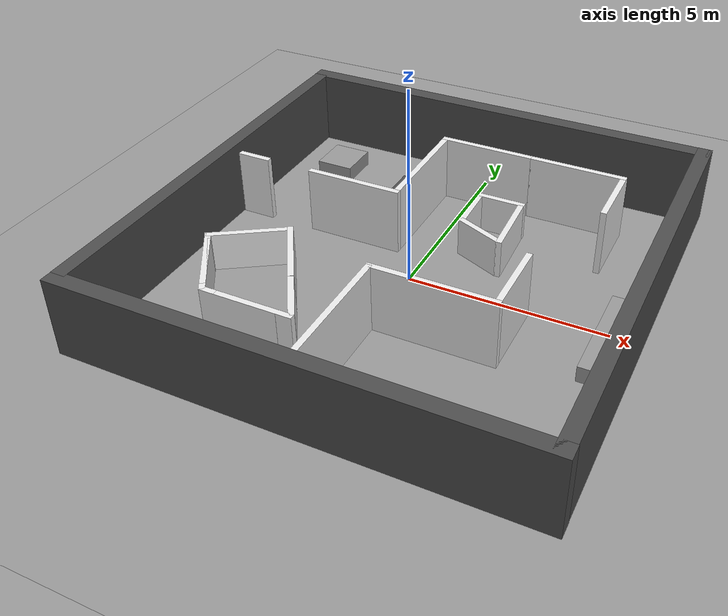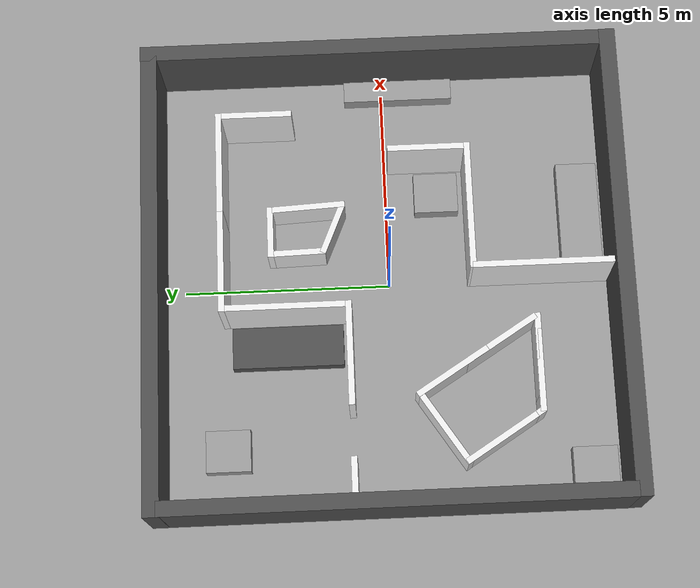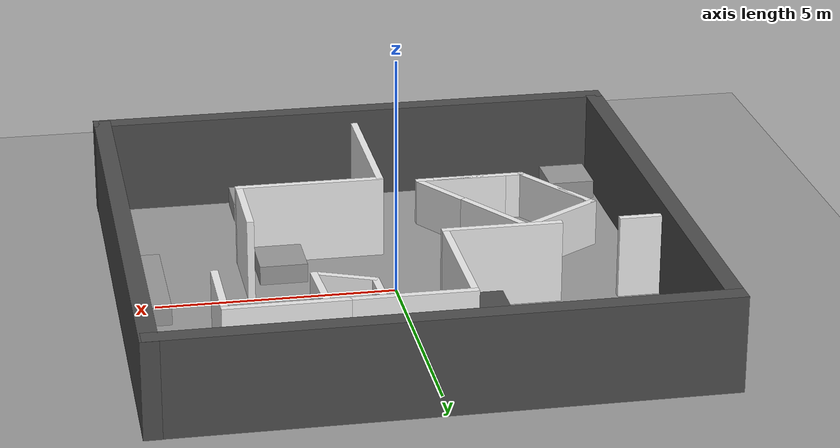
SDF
<sdf version='1.6'>
  <world name='default'>
    <light name='sun' type='directional'>
      <cast_shadows>1</cast_shadows>
      <pose frame=''>0 0 10 0 -0 0</pose>
      <diffuse>0.8 0.8 0.8 1</diffuse>
      <specular>0.2 0.2 0.2 1</specular>
      <attenuation>
        <range>1000</range>
        <constant>0.9</constant>
        <linear>0.01</linear>
        <quadratic>0.001</quadratic>
      </attenuation>
      <direction>0.5 0.1 -0.9</direction>
    </light>
    <scene>
      <ambient>0.4 0.4 0.4 1</ambient>
      <background>0.7 0.7 0.7 1</background>
      <shadows>1</shadows>
    </scene>
    <physics name='default_physics' default='0' type='ode'>
      <max_step_size>0.01</max_step_size>
      <real_time_factor>1</real_time_factor>
      <real_time_update_rate>100</real_time_update_rate>
    </physics>
    <model name='ground_plane_0'>
      <static>1</static>
      <link name='link'>
        <collision name='collision'>
          <geometry>
            <plane>
              <normal>0 0 1</normal>
              <size>100 100</size>
            </plane>
          </geometry>
          <surface>
            <friction>
              <ode>
                <mu>100</mu>
                <mu2>50</mu2>
              </ode>
              <torsional>
                <ode/>
              </torsional>
            </friction>
            <bounce/>
            <contact>
              <ode/>
            </contact>
          </surface>
          <max_contacts>10</max_contacts>
        </collision>
        <visual name='visual'>
          <cast_shadows>0</cast_shadows>
          <geometry>
            <plane>
              <normal>0 0 1</normal>
              <size>100 100</size>
            </plane>
          </geometry>
          <material>
            <script>
              <uri>file://media/materials/scripts/gazebo.material</uri>
              <name>Gazebo/Grey</name>
            </script>
          </material>
        </visual>
        <velocity_decay>
          <linear>0</linear>
          <angular>0</angular>
        </velocity_decay>
        <self_collide>0</self_collide>
        <kinematic>0</kinematic>
        <gravity>1</gravity>
      </link>
      <pose frame=''>0.497681 0 0 0 -0 0</pose>
    </model>
    <model name='Obstacles'>
    <link name='Wall_11'>
      <pose frame=''>-2 1 0 0 -0 0</pose>
      <inertial>
        <mass>2.43558</mass>
        <pose frame=''>0 0 0 0 -0 0</pose>
        <inertia>
          <ixx>8.44174</ixx>
          <ixy>0</ixy>
          <ixz>0</ixz>
          <iyy>8.44174</iyy>
          <iyz>0</iyz>
          <izz>2.43558</izz>
        </inertia>
      </inertial>
      <self_collide>0</self_collide>
      <kinematic>0</kinematic>
      <visual name='Wall_11_Visual'>
        <pose frame=''>0 0 0.5 0 -0 0</pose>
        <geometry>
          <box>
            <size>2.5 0.15 2.43558</size>
          </box>
        </geometry>
        <material>
          <script>
            <uri>file://media/materials/scripts/gazebo.material</uri>
            <name>Gazebo/White</name>
          </script>
          <ambient>1 1 1 1</ambient>
          <diffuse>1 1 1 1</diffuse>
          <specular>0 0 0 1</specular>
          <emissive>0 0 0 1</emissive>
          <shader type='vertex'>
            <normal_map>__default__</normal_map>
          </shader>
        </material>
        <meta>
          <layer>0</layer>
        </meta>
        <cast_shadows>1</cast_shadows>
        <transparency>0</transparency>
      </visual>
      <collision name='Wall_11_Collision'>
        <laser_retro>0</laser_retro>
        <max_contacts>10</max_contacts>
        <pose frame=''>0 0 0.5 0 -0 0</pose>
        <geometry>
          <box>
            <size>2.5 0.15 2.43558</size>
          </box>
        </geometry>
        <surface>
          <friction>
            <ode>
              <mu>1</mu>
              <mu2>1</mu2>
              <fdir1>0 0 0</fdir1>
              <slip1>0</slip1>
              <slip2>0</slip2>
            </ode>
            <torsional>
              <coefficient>1</coefficient>
              <patch_radius>0</patch_radius>
              <surface_radius>0</surface_radius>
              <use_patch_radius>1</use_patch_radius>
              <ode>
                <slip>0</slip>
              </ode>
            </torsional>
          </friction>
          <bounce>
            <restitution_coefficient>0</restitution_coefficient>
            <threshold>1e+06</threshold>
          </bounce>
          <contact>
            <collide_without_contact>0</collide_without_contact>
            <collide_without_contact_bitmask>1</collide_without_contact_bitmask>
            <collide_bitmask>1</collide_bitmask>
            <ode>
              <soft_cfm>0</soft_cfm>
              <soft_erp>0.2</soft_erp>
              <kp>1e+13</kp>
              <kd>1</kd>
              <max_vel>0.01</max_vel>
              <min_depth>0</min_depth>
            </ode>
            <bullet>
              <split_impulse>1</split_impulse>
              <split_impulse_penetration_threshold>-0.01</split_impulse_penetration_threshold>
              <soft_cfm>0</soft_cfm>
              <soft_erp>0.2</soft_erp>
              <kp>1e+13</kp>
              <kd>1</kd>
            </bullet>
          </contact>
        </surface>
      </collision>
    </link>
    <link name='Wall_11_clone'>
      <pose frame=''>0.349144 4 0 0 -0 0</pose>
      <inertial>
        <mass>2.43558</mass>
        <pose frame=''>0 0 0 0 -0 0</pose>
        <inertia>
          <ixx>8.44174</ixx>
          <ixy>0</ixy>
          <ixz>0</ixz>
          <iyy>8.44174</iyy>
          <iyz>0</iyz>
          <izz>2.43558</izz>
        </inertia>
      </inertial>
      <self_collide>0</self_collide>
      <kinematic>0</kinematic>
      <visual name='Wall_11_Visual'>
        <pose frame=''>0 0 0.5 0 -0 0</pose>
        <geometry>
          <box>
            <size>2.5 0.15 2.43558</size>
          </box>
        </geometry>
        <material>
          <script>
            <uri>file://media/materials/scripts/gazebo.material</uri>
            <name>Gazebo/White</name>
          </script>
          <ambient>1 1 1 1</ambient>
          <diffuse>1 1 1 1</diffuse>
          <specular>0 0 0 1</specular>
          <emissive>0 0 0 1</emissive>
          <shader type='vertex'>
            <normal_map>__default__</normal_map>
          </shader>
        </material>
        <meta>
          <layer>0</layer>
        </meta>
        <cast_shadows>1</cast_shadows>
        <transparency>0</transparency>
      </visual>
      <collision name='Wall_11_Collision'>
        <laser_retro>0</laser_retro>
        <max_contacts>10</max_contacts>
        <pose frame=''>0 0 0.5 0 -0 0</pose>
        <geometry>
          <box>
            <size>2.5 0.15 2.43558</size>
          </box>
        </geometry>
        <surface>
          <friction>
            <ode>
              <mu>1</mu>
              <mu2>1</mu2>
              <fdir1>0 0 0</fdir1>
              <slip1>0</slip1>
              <slip2>0</slip2>
            </ode>
            <torsional>
              <coefficient>1</coefficient>
              <patch_radius>0</patch_radius>
              <surface_radius>0</surface_radius>
              <use_patch_radius>1</use_patch_radius>
              <ode>
                <slip>0</slip>
              </ode>
            </torsional>
          </friction>
          <bounce>
            <restitution_coefficient>0</restitution_coefficient>
            <threshold>1e+06</threshold>
          </bounce>
          <contact>
            <collide_without_contact>0</collide_without_contact>
            <collide_without_contact_bitmask>1</collide_without_contact_bitmask>
            <collide_bitmask>1</collide_bitmask>
            <ode>
              <soft_cfm>0</soft_cfm>
              <soft_erp>0.2</soft_erp>
              <kp>1e+13</kp>
              <kd>1</kd>
              <max_vel>0.01</max_vel>
              <min_depth>0</min_depth>
            </ode>
            <bullet>
              <split_impulse>1</split_impulse>
              <split_impulse_penetration_threshold>-0.01</split_impulse_penetration_threshold>
              <soft_cfm>0</soft_cfm>
              <soft_erp>0.2</soft_erp>
              <kp>1e+13</kp>
              <kd>1</kd>
            </bullet>
          </contact>
        </surface>
      </collision>
    </link>
    <link name='Wall_11_clone_0'>
      <pose frame=''>-0.826002 2.50053 0 0 0 -1.5708</pose>
      <inertial>
        <mass>2.78329</mass>
        <pose frame=''>0 0 0 0 -0 0</pose>
        <inertia>
          <ixx>9.64467</ixx>
          <ixy>0</ixy>
          <ixz>0</ixz>
          <iyy>10.0709</iyy>
          <iyz>0</iyz>
          <izz>3.20952</izz>
        </inertia>
      </inertial>
      <self_collide>0</self_collide>
      <kinematic>0</kinematic>
      <visual name='Wall_11_Visual'>
        <pose frame=''>0 0 0.5 0 -0 0</pose>
        <geometry>
          <box>
            <size>2.85731 0.15 2.43521</size>
          </box>
        </geometry>
        <material>
          <script>
            <uri>file://media/materials/scripts/gazebo.material</uri>
            <name>Gazebo/White</name>
          </script>
          <ambient>1 1 1 1</ambient>
          <diffuse>1 1 1 1</diffuse>
          <specular>0 0 0 1</specular>
          <emissive>0 0 0 1</emissive>
          <shader type='vertex'>
            <normal_map>__default__</normal_map>
          </shader>
        </material>
        <meta>
          <layer>0</layer>
        </meta>
        <cast_shadows>1</cast_shadows>
        <transparency>0</transparency>
      </visual>
      <collision name='Wall_11_Collision'>
        <laser_retro>0</laser_retro>
        <max_contacts>10</max_contacts>
        <pose frame=''>0 0 0.5 0 -0 0</pose>
        <geometry>
          <box>
            <size>2.85731 0.15 2.43521</size>
          </box>
        </geometry>
        <surface>
          <friction>
            <ode>
              <mu>1</mu>
              <mu2>1</mu2>
              <fdir1>0 0 0</fdir1>
              <slip1>0</slip1>
              <slip2>0</slip2>
            </ode>
            <torsional>
              <coefficient>1</coefficient>
              <patch_radius>0</patch_radius>
              <surface_radius>0</surface_radius>
              <use_patch_radius>1</use_patch_radius>
              <ode>
                <slip>0</slip>
              </ode>
            </torsional>
          </friction>
          <bounce>
            <restitution_coefficient>0</restitution_coefficient>
            <threshold>1e+06</threshold>
          </bounce>
          <contact>
            <collide_without_contact>0</collide_without_contact>
            <collide_without_contact_bitmask>1</collide_without_contact_bitmask>
            <collide_bitmask>1</collide_bitmask>
            <ode>
              <soft_cfm>0</soft_cfm>
              <soft_erp>0.2</soft_erp>
              <kp>1e+13</kp>
              <kd>1</kd>
              <max_vel>0.01</max_vel>
              <min_depth>0</min_depth>
            </ode>
            <bullet>
              <split_impulse>1</split_impulse>
              <split_impulse_penetration_threshold>-0.01</split_impulse_penetration_threshold>
              <soft_cfm>0</soft_cfm>
              <soft_erp>0.2</soft_erp>
              <kp>1e+13</kp>
              <kd>1</kd>
            </bullet>
          </contact>
        </surface>
      </collision>
    </link>
    <link name='Wall_11_clone_0_clone'>
      <pose frame=''>4 3.14359 0 0 0 -1.5708</pose>
      <inertial>
        <mass>1.80348</mass>
        <pose frame=''>0 0 0 0 -0 0</pose>
        <inertia>
          <ixx>6.24942</ixx>
          <ixy>0</ixy>
          <ixz>0</ixz>
          <iyy>5.84224</iyy>
          <iyz>0</iyz>
          <izz>1.3963</izz>
        </inertia>
      </inertial>
      <self_collide>0</self_collide>
      <kinematic>0</kinematic>
      <visual name='Wall_11_Visual'>
        <pose frame=''>0 0 0.5 0 -0 0</pose>
        <geometry>
          <box>
            <size>1.85143 0.15 2.43521</size>
          </box>
        </geometry>
        <material>
          <script>
            <uri>file://media/materials/scripts/gazebo.material</uri>
            <name>Gazebo/White</name>
          </script>
          <ambient>1 1 1 1</ambient>
          <diffuse>1 1 1 1</diffuse>
          <specular>0 0 0 1</specular>
          <emissive>0 0 0 1</emissive>
          <shader type='vertex'>
            <normal_map>__default__</normal_map>
          </shader>
        </material>
        <meta>
          <layer>0</layer>
        </meta>
        <cast_shadows>1</cast_shadows>
        <transparency>0</transparency>
      </visual>
      <collision name='Wall_11_Collision'>
        <laser_retro>0</laser_retro>
        <max_contacts>10</max_contacts>
        <pose frame=''>0 0 0.5 0 -0 0</pose>
        <geometry>
          <box>
            <size>1.85143 0.15 2.43521</size>
          </box>
        </geometry>
        <surface>
          <friction>
            <ode>
              <mu>1</mu>
              <mu2>1</mu2>
              <fdir1>0 0 0</fdir1>
              <slip1>0</slip1>
              <slip2>0</slip2>
            </ode>
            <torsional>
              <coefficient>1</coefficient>
              <patch_radius>0</patch_radius>
              <surface_radius>0</surface_radius>
              <use_patch_radius>1</use_patch_radius>
              <ode>
                <slip>0</slip>
              </ode>
            </torsional>
          </friction>
          <bounce>
            <restitution_coefficient>0</restitution_coefficient>
            <threshold>1e+06</threshold>
          </bounce>
          <contact>
            <collide_without_contact>0</collide_without_contact>
            <collide_without_contact_bitmask>1</collide_without_contact_bitmask>
            <collide_bitmask>1</collide_bitmask>
            <ode>
              <soft_cfm>0</soft_cfm>
              <soft_erp>0.2</soft_erp>
              <kp>1e+13</kp>
              <kd>1</kd>
              <max_vel>0.01</max_vel>
              <min_depth>0</min_depth>
            </ode>
            <bullet>
              <split_impulse>1</split_impulse>
              <split_impulse_penetration_threshold>-0.01</split_impulse_penetration_threshold>
              <soft_cfm>0</soft_cfm>
              <soft_erp>0.2</soft_erp>
              <kp>1e+13</kp>
              <kd>1</kd>
            </bullet>
          </contact>
        </surface>
      </collision>
    </link>
    <link name='Wall_11_clone_0_clone_0'>
      <pose frame=''>1e-06 -3.69525 0 0 0 -1.5708</pose>
      <inertial>
        <mass>3.33251</mass>
        <pose frame=''>0 0 0 0 -0 0</pose>
        <inertia>
          <ixx>11.5478</ixx>
          <ixy>0</ixy>
          <ixz>0</ixz>
          <iyy>13.0019</iyy>
          <iyz>0</iyz>
          <izz>4.78661</izz>
        </inertia>
      </inertial>
      <self_collide>0</self_collide>
      <kinematic>0</kinematic>
      <gravity>1</gravity>
      <visual name='Wall_11_Visual'>
        <pose frame=''>0 0 0.5 0 -0 0</pose>
        <geometry>
          <box>
            <size>3.42114 0.15 2.43521</size>
          </box>
        </geometry>
        <material>
          <script>
            <uri>file://media/materials/scripts/gazebo.material</uri>
            <name>Gazebo/White</name>
          </script>
          <ambient>1 1 1 1</ambient>
          <diffuse>1 1 1 1</diffuse>
          <specular>0 0 0 1</specular>
          <emissive>0 0 0 1</emissive>
          <shader type='vertex'>
            <normal_map>__default__</normal_map>
          </shader>
        </material>
        <meta>
          <layer>0</layer>
        </meta>
        <cast_shadows>1</cast_shadows>
        <transparency>0</transparency>
      </visual>
      <collision name='Wall_11_Collision'>
        <laser_retro>0</laser_retro>
        <max_contacts>10</max_contacts>
        <pose frame=''>0 0 0.5 0 -0 0</pose>
        <geometry>
          <box>
            <size>3.42114 0.15 2.43521</size>
          </box>
        </geometry>
        <surface>
          <friction>
            <ode>
              <mu>1</mu>
              <mu2>1</mu2>
              <fdir1>0 0 0</fdir1>
              <slip1>0</slip1>
              <slip2>0</slip2>
            </ode>
            <torsional>
              <coefficient>1</coefficient>
              <patch_radius>0</patch_radius>
              <surface_radius>0</surface_radius>
              <use_patch_radius>1</use_patch_radius>
              <ode>
                <slip>0</slip>
              </ode>
            </torsional>
          </friction>
          <bounce>
            <restitution_coefficient>0</restitution_coefficient>
            <threshold>1e+06</threshold>
          </bounce>
          <contact>
            <collide_without_contact>0</collide_without_contact>
            <collide_without_contact_bitmask>1</collide_without_contact_bitmask>
            <collide_bitmask>1</collide_bitmask>
            <ode>
              <soft_cfm>0</soft_cfm>
              <soft_erp>0.2</soft_erp>
              <kp>1e+13</kp>
              <kd>1</kd>
              <max_vel>0.01</max_vel>
              <min_depth>0</min_depth>
            </ode>
            <bullet>
              <split_impulse>1</split_impulse>
              <split_impulse_penetration_threshold>-0.01</split_impulse_penetration_threshold>
              <soft_cfm>0</soft_cfm>
              <soft_erp>0.2</soft_erp>
              <kp>1e+13</kp>
              <kd>1</kd>
            </bullet>
          </contact>
        </surface>
      </collision>
    </link>
    <link name='Wall_11_clone_0_clone_0_clone'>
      <pose frame=''>1.50155 -2 0 0 -0 3.14159</pose>
      <inertial>
        <mass>3.07107</mass>
        <pose frame=''>0 0 0 0 -0 0</pose>
        <inertia>
          <ixx>10.6418</ixx>
          <ixy>0</ixy>
          <ixz>0</ixz>
          <iyy>11.5484</iyy>
          <iyz>0</iyz>
          <izz>3.9776</izz>
        </inertia>
      </inertial>
      <self_collide>0</self_collide>
      <kinematic>0</kinematic>
      <visual name='Wall_11_Visual'>
        <pose frame=''>0 0 0.5 0 -0 0</pose>
        <geometry>
          <box>
            <size>3.15274 0.15 2.43521</size>
          </box>
        </geometry>
        <material>
          <script>
            <uri>file://media/materials/scripts/gazebo.material</uri>
            <name>Gazebo/White</name>
          </script>
          <ambient>1 1 1 1</ambient>
          <diffuse>1 1 1 1</diffuse>
          <specular>0 0 0 1</specular>
          <emissive>0 0 0 1</emissive>
          <shader type='vertex'>
            <normal_map>__default__</normal_map>
          </shader>
        </material>
        <meta>
          <layer>0</layer>
        </meta>
        <cast_shadows>1</cast_shadows>
        <transparency>0</transparency>
      </visual>
      <collision name='Wall_11_Collision'>
        <laser_retro>0</laser_retro>
        <max_contacts>10</max_contacts>
        <pose frame=''>0 0 0.5 0 -0 0</pose>
        <geometry>
          <box>
            <size>3.15274 0.15 2.43521</size>
          </box>
        </geometry>
        <surface>
          <friction>
            <ode>
              <mu>1</mu>
              <mu2>1</mu2>
              <fdir1>0 0 0</fdir1>
              <slip1>0</slip1>
              <slip2>0</slip2>
            </ode>
            <torsional>
              <coefficient>1</coefficient>
              <patch_radius>0</patch_radius>
              <surface_radius>0</surface_radius>
              <use_patch_radius>1</use_patch_radius>
              <ode>
                <slip>0</slip>
              </ode>
            </torsional>
          </friction>
          <bounce>
            <restitution_coefficient>0</restitution_coefficient>
            <threshold>1e+06</threshold>
          </bounce>
          <contact>
            <collide_without_contact>0</collide_without_contact>
            <collide_without_contact_bitmask>1</collide_without_contact_bitmask>
            <collide_bitmask>1</collide_bitmask>
            <ode>
              <soft_cfm>0</soft_cfm>
              <soft_erp>0.2</soft_erp>
              <kp>1e+13</kp>
              <kd>1</kd>
              <max_vel>0.01</max_vel>
              <min_depth>0</min_depth>
            </ode>
            <bullet>
              <split_impulse>1</split_impulse>
              <split_impulse_penetration_threshold>-0.01</split_impulse_penetration_threshold>
              <soft_cfm>0</soft_cfm>
              <soft_erp>0.2</soft_erp>
              <kp>1e+13</kp>
              <kd>1</kd>
            </bullet>
          </contact>
        </surface>
      </collision>
    </link>
    <link name='Wall_11_clone_0_clone_clone'>
      <pose frame=''>3 -1 0 0 0 -1.5708</pose>
      <inertial>
        <mass>1.80348</mass>
        <pose frame=''>0 0 0 0 -0 0</pose>
        <inertia>
          <ixx>6.24942</ixx>
          <ixy>0</ixy>
          <ixz>0</ixz>
          <iyy>5.84224</iyy>
          <iyz>0</iyz>
          <izz>1.3963</izz>
        </inertia>
      </inertial>
      <self_collide>0</self_collide>
      <kinematic>0</kinematic>
      <visual name='Wall_11_Visual'>
        <pose frame=''>0 0 0.5 0 -0 0</pose>
        <geometry>
          <box>
            <size>1.85143 0.15 2.43521</size>
          </box>
        </geometry>
        <material>
          <script>
            <uri>file://media/materials/scripts/gazebo.material</uri>
            <name>Gazebo/White</name>
          </script>
          <ambient>1 1 1 1</ambient>
          <diffuse>1 1 1 1</diffuse>
          <specular>0 0 0 1</specular>
          <emissive>0 0 0 1</emissive>
          <shader type='vertex'>
            <normal_map>__default__</normal_map>
          </shader>
        </material>
        <meta>
          <layer>0</layer>
        </meta>
        <cast_shadows>1</cast_shadows>
        <transparency>0</transparency>
      </visual>
      <collision name='Wall_11_Collision'>
        <laser_retro>0</laser_retro>
        <max_contacts>10</max_contacts>
        <pose frame=''>0 0 0.5 0 -0 0</pose>
        <geometry>
          <box>
            <size>1.85143 0.15 2.43521</size>
          </box>
        </geometry>
        <surface>
          <friction>
            <ode>
              <mu>1</mu>
              <mu2>1</mu2>
              <fdir1>0 0 0</fdir1>
              <slip1>0</slip1>
              <slip2>0</slip2>
            </ode>
            <torsional>
              <coefficient>1</coefficient>
              <patch_radius>0</patch_radius>
              <surface_radius>0</surface_radius>
              <use_patch_radius>1</use_patch_radius>
              <ode>
                <slip>0</slip>
              </ode>
            </torsional>
          </friction>
          <bounce>
            <restitution_coefficient>0</restitution_coefficient>
            <threshold>1e+06</threshold>
          </bounce>
          <contact>
            <collide_without_contact>0</collide_without_contact>
            <collide_without_contact_bitmask>1</collide_without_contact_bitmask>
            <collide_bitmask>1</collide_bitmask>
            <ode>
              <soft_cfm>0</soft_cfm>
              <soft_erp>0.2</soft_erp>
              <kp>1e+13</kp>
              <kd>1</kd>
              <max_vel>0.01</max_vel>
              <min_depth>0</min_depth>
            </ode>
            <bullet>
              <split_impulse>1</split_impulse>
              <split_impulse_penetration_threshold>-0.01</split_impulse_penetration_threshold>
              <soft_cfm>0</soft_cfm>
              <soft_erp>0.2</soft_erp>
              <kp>1e+13</kp>
              <kd>1</kd>
            </bullet>
          </contact>
        </surface>
      </collision>
    </link>
    <link name='Wall_11_clone_1'>
      <pose frame=''>-4.89998 1 0 0 -0 0</pose>
      <inertial>
        <mass>0.880522</mass>
        <pose frame=''>0 0 0 0 -0 0</pose>
        <inertia>
          <ixx>3.0519</ixx>
          <ixy>0</ixy>
          <ixz>0</ixz>
          <iyy>2.66918</iyy>
          <iyz>0</iyz>
          <izz>0.497803</izz>
        </inertia>
      </inertial>
      <self_collide>0</self_collide>
      <kinematic>0</kinematic>
      <gravity>1</gravity>
      <visual name='Wall_11_Visual'>
        <pose frame=''>0 0 0.5 0 -0 0</pose>
        <geometry>
          <box>
            <size>0.903814 0.15 2.43558</size>
          </box>
        </geometry>
        <material>
          <script>
            <uri>file://media/materials/scripts/gazebo.material</uri>
            <name>Gazebo/White</name>
          </script>
          <ambient>1 1 1 1</ambient>
          <diffuse>1 1 1 1</diffuse>
          <specular>0 0 0 1</specular>
          <emissive>0 0 0 1</emissive>
          <shader type='vertex'>
            <normal_map>__default__</normal_map>
          </shader>
        </material>
        <meta>
          <layer>0</layer>
        </meta>
        <cast_shadows>1</cast_shadows>
        <transparency>0</transparency>
      </visual>
      <collision name='Wall_11_Collision'>
        <laser_retro>0</laser_retro>
        <max_contacts>10</max_contacts>
        <pose frame=''>0 0 0.5 0 -0 0</pose>
        <geometry>
          <box>
            <size>0.903814 0.15 2.43558</size>
          </box>
        </geometry>
        <surface>
          <friction>
            <ode>
              <mu>1</mu>
              <mu2>1</mu2>
              <fdir1>0 0 0</fdir1>
              <slip1>0</slip1>
              <slip2>0</slip2>
            </ode>
            <torsional>
              <coefficient>1</coefficient>
              <patch_radius>0</patch_radius>
              <surface_radius>0</surface_radius>
              <use_patch_radius>1</use_patch_radius>
              <ode>
                <slip>0</slip>
              </ode>
            </torsional>
          </friction>
          <bounce>
            <restitution_coefficient>0</restitution_coefficient>
            <threshold>1e+06</threshold>
          </bounce>
          <contact>
            <collide_without_contact>0</collide_without_contact>
            <collide_without_contact_bitmask>1</collide_without_contact_bitmask>
            <collide_bitmask>1</collide_bitmask>
            <ode>
              <soft_cfm>0</soft_cfm>
              <soft_erp>0.2</soft_erp>
              <kp>1e+13</kp>
              <kd>1</kd>
              <max_vel>0.01</max_vel>
              <min_depth>0</min_depth>
            </ode>
            <bullet>
              <split_impulse>1</split_impulse>
              <split_impulse_penetration_threshold>-0.01</split_impulse_penetration_threshold>
              <soft_cfm>0</soft_cfm>
              <soft_erp>0.2</soft_erp>
              <kp>1e+13</kp>
              <kd>1</kd>
            </bullet>
          </contact>
        </surface>
      </collision>
    </link>
    <link name='Wall_11_clone_clone'>
      <pose frame=''>2.82281 4 0 0 -0 0</pose>
      <inertial>
        <mass>2.43558</mass>
        <pose frame=''>0 0 0 0 -0 0</pose>
        <inertia>
          <ixx>8.44174</ixx>
          <ixy>0</ixy>
          <ixz>0</ixz>
          <iyy>8.44174</iyy>
          <iyz>0</iyz>
          <izz>2.43558</izz>
        </inertia>
      </inertial>
      <self_collide>0</self_collide>
      <kinematic>0</kinematic>
      <visual name='Wall_11_Visual'>
        <pose frame=''>0 0 0.5 0 -0 0</pose>
        <geometry>
          <box>
            <size>2.5 0.15 2.43558</size>
          </box>
        </geometry>
        <material>
          <script>
            <uri>file://media/materials/scripts/gazebo.material</uri>
            <name>Gazebo/White</name>
          </script>
          <ambient>1 1 1 1</ambient>
          <diffuse>1 1 1 1</diffuse>
          <specular>0 0 0 1</specular>
          <emissive>0 0 0 1</emissive>
          <shader type='vertex'>
            <normal_map>__default__</normal_map>
          </shader>
        </material>
        <meta>
          <layer>0</layer>
        </meta>
        <cast_shadows>1</cast_shadows>
        <transparency>0</transparency>
      </visual>
      <collision name='Wall_11_Collision'>
        <laser_retro>0</laser_retro>
        <max_contacts>10</max_contacts>
        <pose frame=''>0 0 0.5 0 -0 0</pose>
        <geometry>
          <box>
            <size>2.5 0.15 2.43558</size>
          </box>
        </geometry>
        <surface>
          <friction>
            <ode>
              <mu>1</mu>
              <mu2>1</mu2>
              <fdir1>0 0 0</fdir1>
              <slip1>0</slip1>
              <slip2>0</slip2>
            </ode>
            <torsional>
              <coefficient>1</coefficient>
              <patch_radius>0</patch_radius>
              <surface_radius>0</surface_radius>
              <use_patch_radius>1</use_patch_radius>
              <ode>
                <slip>0</slip>
              </ode>
            </torsional>
          </friction>
          <bounce>
            <restitution_coefficient>0</restitution_coefficient>
            <threshold>1e+06</threshold>
          </bounce>
          <contact>
            <collide_without_contact>0</collide_without_contact>
            <collide_without_contact_bitmask>1</collide_without_contact_bitmask>
            <collide_bitmask>1</collide_bitmask>
            <ode>
              <soft_cfm>0</soft_cfm>
              <soft_erp>0.2</soft_erp>
              <kp>1e+13</kp>
              <kd>1</kd>
              <max_vel>0.01</max_vel>
              <min_depth>0</min_depth>
            </ode>
            <bullet>
              <split_impulse>1</split_impulse>
              <split_impulse_penetration_threshold>-0.01</split_impulse_penetration_threshold>
              <soft_cfm>0</soft_cfm>
              <soft_erp>0.2</soft_erp>
              <kp>1e+13</kp>
              <kd>1</kd>
            </bullet>
          </contact>
        </surface>
      </collision>
    </link>
    <link name='Wall_15'>
      <pose frame=''>1.22585 2.84413 0 0 -0 0</pose>
      <self_collide>0</self_collide>
      <kinematic>0</kinematic>
      <gravity>1</gravity>
      <inertial>
        <mass>1</mass>
        <pose frame=''>0 0 0 0 -0 0</pose>
        <inertia>
          <ixx>1</ixx>
          <ixy>0</ixy>
          <ixz>0</ixz>
          <iyy>1</iyy>
          <iyz>0</iyz>
          <izz>1</izz>
        </inertia>
      </inertial>
      <visual name='Wall_15_Visual'>
        <pose frame=''>0 0 0.5 0 -0 0</pose>
        <geometry>
          <box>
            <size>1.2678 0.15 1</size>
          </box>
        </geometry>
        <material>
          <script>
            <uri>file://media/materials/scripts/gazebo.material</uri>
            <name>Gazebo/White</name>
          </script>
          <ambient>1 1 1 1</ambient>
          <diffuse>1 1 1 1</diffuse>
          <specular>0.2 0.2 0.2 1</specular>
          <emissive>0 0 0 1</emissive>
          <shader type='vertex'>
            <normal_map>__default__</normal_map>
          </shader>
        </material>
        <meta>
          <layer>0</layer>
        </meta>
        <cast_shadows>1</cast_shadows>
        <transparency>0</transparency>
      </visual>
      <collision name='Wall_15_Collision'>
        <laser_retro>0</laser_retro>
        <max_contacts>10</max_contacts>
        <pose frame=''>0 0 0.5 0 -0 0</pose>
        <geometry>
          <box>
            <size>1.2678 0.15 1</size>
          </box>
        </geometry>
        <surface>
          <friction>
            <ode>
              <mu>1</mu>
              <mu2>1</mu2>
              <fdir1>0 0 0</fdir1>
              <slip1>0</slip1>
              <slip2>0</slip2>
            </ode>
            <torsional>
              <coefficient>1</coefficient>
              <patch_radius>0</patch_radius>
              <surface_radius>0</surface_radius>
              <use_patch_radius>1</use_patch_radius>
              <ode>
                <slip>0</slip>
              </ode>
            </torsional>
          </friction>
          <bounce>
            <restitution_coefficient>0</restitution_coefficient>
            <threshold>1e+06</threshold>
          </bounce>
          <contact>
            <collide_without_contact>0</collide_without_contact>
            <collide_without_contact_bitmask>1</collide_without_contact_bitmask>
            <collide_bitmask>1</collide_bitmask>
            <ode>
              <soft_cfm>0</soft_cfm>
              <soft_erp>0.2</soft_erp>
              <kp>1e+13</kp>
              <kd>1</kd>
              <max_vel>0.01</max_vel>
              <min_depth>0</min_depth>
            </ode>
            <bullet>
              <split_impulse>1</split_impulse>
              <split_impulse_penetration_threshold>-0.01</split_impulse_penetration_threshold>
              <soft_cfm>0</soft_cfm>
              <soft_erp>0.2</soft_erp>
              <kp>1e+13</kp>
              <kd>1</kd>
            </bullet>
          </contact>
        </surface>
      </collision>
    </link>
    <link name='Wall_16'>
      <pose frame=''>1.82764 1.90397 3.1e-05 0 0 -1.52005</pose>
      <self_collide>0</self_collide>
      <kinematic>0</kinematic>
      <inertial>
        <inertia>
          <ixx>1.79769e+308</ixx>
          <ixy>0</ixy>
          <ixz>0</ixz>
          <iyy>1.79769e+308</iyy>
          <iyz>0</iyz>
          <izz>1.79769e+308</izz>
        </inertia>
        <mass>0</mass>
        <pose frame=''>0 0 0 0 -0 0</pose>
      </inertial>
      <gravity>1</gravity>
      <visual name='Wall_16_Visual'>
        <pose frame=''>0 0 0.5 0 -0 0</pose>
        <geometry>
          <box>
            <size>1.7797 0.15 1</size>
          </box>
        </geometry>
        <material>
          <script>
            <uri>file://media/materials/scripts/gazebo.material</uri>
            <name>Gazebo/White</name>
          </script>
          <ambient>1 1 1 1</ambient>
          <diffuse>1 1 1 1</diffuse>
          <specular>0.2 0.2 0.2 1</specular>
          <emissive>0 0 0 1</emissive>
          <shader type='vertex'>
            <normal_map>__default__</normal_map>
          </shader>
        </material>
        <meta>
          <layer>0</layer>
        </meta>
        <cast_shadows>1</cast_shadows>
        <transparency>0</transparency>
      </visual>
      <collision name='Wall_16_Collision'>
        <laser_retro>0</laser_retro>
        <max_contacts>10</max_contacts>
        <pose frame=''>0 0 0.5 0 -0 0</pose>
        <geometry>
          <box>
            <size>1.7797 0.15 1</size>
          </box>
        </geometry>
        <surface>
          <friction>
            <ode>
              <mu>1</mu>
              <mu2>1</mu2>
              <fdir1>0 0 0</fdir1>
              <slip1>0</slip1>
              <slip2>0</slip2>
            </ode>
            <torsional>
              <coefficient>1</coefficient>
              <patch_radius>0</patch_radius>
              <surface_radius>0</surface_radius>
              <use_patch_radius>1</use_patch_radius>
              <ode>
                <slip>0</slip>
              </ode>
            </torsional>
          </friction>
          <bounce>
            <restitution_coefficient>0</restitution_coefficient>
            <threshold>1e+06</threshold>
          </bounce>
          <contact>
            <collide_without_contact>0</collide_without_contact>
            <collide_without_contact_bitmask>1</collide_without_contact_bitmask>
            <collide_bitmask>1</collide_bitmask>
            <ode>
              <soft_cfm>0</soft_cfm>
              <soft_erp>0.2</soft_erp>
              <kp>1e+13</kp>
              <kd>1</kd>
              <max_vel>0.01</max_vel>
              <min_depth>0</min_depth>
            </ode>
            <bullet>
              <split_impulse>1</split_impulse>
              <split_impulse_penetration_threshold>-0.01</split_impulse_penetration_threshold>
              <soft_cfm>0</soft_cfm>
              <soft_erp>0.2</soft_erp>
              <kp>1e+13</kp>
              <kd>1</kd>
            </bullet>
          </contact>
        </surface>
      </collision>
    </link>
    <link name='Wall_17'>
      <pose frame=''>1.24744 1.3314 0 0 -0 2.73868</pose>
      <inertial>
        <mass>1.0293</mass>
        <pose frame=''>0 0 0 0 -0 0</pose>
        <inertia>
          <ixx>1.0293</ixx>
          <ixy>0</ixy>
          <ixz>0</ixz>
          <iyy>1.0599</iyy>
          <iyz>0</iyz>
          <izz>1.0599</izz>
        </inertia>
      </inertial>
      <self_collide>0</self_collide>
      <kinematic>0</kinematic>
      <gravity>1</gravity>
      <visual name='ModelPreview_1::Wall_17::visual_1'>
        <pose frame=''>0 0 0.5 0 -0 0</pose>
        <geometry>
          <box>
            <size>1.28663 0.15 1</size>
          </box>
        </geometry>
        <material>
          <script>
            <uri>file://media/materials/scripts/gazebo.material</uri>
            <name>Gazebo/White</name>
          </script>
          <ambient>1 1 1 1</ambient>
          <diffuse>1 1 1 1</diffuse>
          <specular>0.2 0.2 0.2 1</specular>
          <emissive>0 0 0 1</emissive>
          <shader type='vertex'>
            <normal_map>__default__</normal_map>
          </shader>
        </material>
        <meta>
          <layer>0</layer>
        </meta>
        <cast_shadows>1</cast_shadows>
        <transparency>0</transparency>
      </visual>
      <collision name='Wall_17_Collision'>
        <laser_retro>0</laser_retro>
        <max_contacts>10</max_contacts>
        <pose frame=''>0 0 0.5 0 -0 0</pose>
        <geometry>
          <box>
            <size>1.28663 0.15 1</size>
          </box>
        </geometry>
        <surface>
          <friction>
            <ode>
              <mu>1</mu>
              <mu2>1</mu2>
              <fdir1>0 0 0</fdir1>
              <slip1>0</slip1>
              <slip2>0</slip2>
            </ode>
            <torsional>
              <coefficient>1</coefficient>
              <patch_radius>0</patch_radius>
              <surface_radius>0</surface_radius>
              <use_patch_radius>1</use_patch_radius>
              <ode>
                <slip>0</slip>
              </ode>
            </torsional>
          </friction>
          <bounce>
            <restitution_coefficient>0</restitution_coefficient>
            <threshold>1e+06</threshold>
          </bounce>
          <contact>
            <collide_without_contact>0</collide_without_contact>
            <collide_without_contact_bitmask>1</collide_without_contact_bitmask>
            <collide_bitmask>1</collide_bitmask>
            <ode>
              <soft_cfm>0</soft_cfm>
              <soft_erp>0.2</soft_erp>
              <kp>1e+13</kp>
              <kd>1</kd>
              <max_vel>0.01</max_vel>
              <min_depth>0</min_depth>
            </ode>
            <bullet>
              <split_impulse>1</split_impulse>
              <split_impulse_penetration_threshold>-0.01</split_impulse_penetration_threshold>
              <soft_cfm>0</soft_cfm>
              <soft_erp>0.2</soft_erp>
              <kp>1e+13</kp>
              <kd>1</kd>
            </bullet>
          </contact>
        </surface>
      </collision>
    </link>
    <link name='Wall_18'>
      <pose frame=''>0.683458 2.14742 0 0 -0 1.59577</pose>
      <self_collide>0</self_collide>
      <kinematic>0</kinematic>
      <gravity>1</gravity>
      <inertial>
        <mass>1.29658</mass>
        <pose frame=''>0 0 0 0 -0 0</pose>
        <inertia>
          <ixx>1.29658</ixx>
          <ixy>0</ixy>
          <ixz>0</ixz>
          <iyy>1.73814</iyy>
          <iyz>0</iyz>
          <izz>1.73814</izz>
        </inertia>
      </inertial>
      <visual name='Wall_18_Visual'>
        <pose frame=''>0 0 0.5 0 -0 0</pose>
        <geometry>
          <box>
            <size>1.25121 0.15 1</size>
          </box>
        </geometry>
        <material>
          <script>
            <uri>file://media/materials/scripts/gazebo.material</uri>
            <name>Gazebo/White</name>
          </script>
          <ambient>1 1 1 1</ambient>
          <diffuse>1 1 1 1</diffuse>
          <specular>0.2 0.2 0.2 1</specular>
          <emissive>0 0 0 1</emissive>
          <shader type='vertex'>
            <normal_map>__default__</normal_map>
          </shader>
        </material>
        <meta>
          <layer>0</layer>
        </meta>
        <cast_shadows>1</cast_shadows>
        <transparency>0</transparency>
      </visual>
      <collision name='Wall_18_Collision'>
        <laser_retro>0</laser_retro>
        <max_contacts>10</max_contacts>
        <pose frame=''>0 0 0.5 0 -0 0</pose>
        <geometry>
          <box>
            <size>1.25121 0.15 1</size>
          </box>
        </geometry>
        <surface>
          <friction>
            <ode>
              <mu>1</mu>
              <mu2>1</mu2>
              <fdir1>0 0 0</fdir1>
              <slip1>0</slip1>
              <slip2>0</slip2>
            </ode>
            <torsional>
              <coefficient>1</coefficient>
              <patch_radius>0</patch_radius>
              <surface_radius>0</surface_radius>
              <use_patch_radius>1</use_patch_radius>
              <ode>
                <slip>0</slip>
              </ode>
            </torsional>
          </friction>
          <bounce>
            <restitution_coefficient>0</restitution_coefficient>
            <threshold>1e+06</threshold>
          </bounce>
          <contact>
            <collide_without_contact>0</collide_without_contact>
            <collide_without_contact_bitmask>1</collide_without_contact_bitmask>
            <collide_bitmask>1</collide_bitmask>
            <ode>
              <soft_cfm>0</soft_cfm>
              <soft_erp>0.2</soft_erp>
              <kp>1e+13</kp>
              <kd>1</kd>
              <max_vel>0.01</max_vel>
              <min_depth>0</min_depth>
            </ode>
            <bullet>
              <split_impulse>1</split_impulse>
              <split_impulse_penetration_threshold>-0.01</split_impulse_penetration_threshold>
              <soft_cfm>0</soft_cfm>
              <soft_erp>0.2</soft_erp>
              <kp>1e+13</kp>
              <kd>1</kd>
            </bullet>
          </contact>
        </surface>
      </collision>
    </link>
    <link name='Wall_24'>
      <pose frame=''>-3.78607 -1.18699 0 0 -0 0.57484</pose>
      <self_collide>0</self_collide>
      <kinematic>0</kinematic>
      <gravity>1</gravity>
      <inertial>
        <mass>1</mass>
        <pose frame=''>0 0 0 0 -0 0</pose>
        <inertia>
          <ixx>1</ixx>
          <ixy>0</ixy>
          <ixz>0</ixz>
          <iyy>1</iyy>
          <iyz>0</iyz>
          <izz>1</izz>
        </inertia>
      </inertial>
      <visual name='Wall_24_Visual'>
        <pose frame=''>0 0 0.5 0 -0 0</pose>
        <geometry>
          <box>
            <size>1.97704 0.15 1</size>
          </box>
        </geometry>
        <material>
          <script>
            <uri>file://media/materials/scripts/gazebo.material</uri>
            <name>Gazebo/White</name>
          </script>
          <ambient>1 1 1 1</ambient>
          <diffuse>1 1 1 1</diffuse>
          <specular>0.2 0.2 0.2 1</specular>
          <emissive>0 0 0 1</emissive>
          <shader type='vertex'>
            <normal_map>__default__</normal_map>
          </shader>
        </material>
        <meta>
          <layer>0</layer>
        </meta>
        <cast_shadows>1</cast_shadows>
        <transparency>0</transparency>
      </visual>
      <collision name='Wall_24_Collision'>
        <laser_retro>0</laser_retro>
        <max_contacts>10</max_contacts>
        <pose frame=''>0 0 0.5 0 -0 0</pose>
        <geometry>
          <box>
            <size>1.97704 0.15 1</size>
          </box>
        </geometry>
        <surface>
          <friction>
            <ode>
              <mu>1</mu>
              <mu2>1</mu2>
              <fdir1>0 0 0</fdir1>
              <slip1>0</slip1>
              <slip2>0</slip2>
            </ode>
            <torsional>
              <coefficient>1</coefficient>
              <patch_radius>0</patch_radius>
              <surface_radius>0</surface_radius>
              <use_patch_radius>1</use_patch_radius>
              <ode>
                <slip>0</slip>
              </ode>
            </torsional>
          </friction>
          <bounce>
            <restitution_coefficient>0</restitution_coefficient>
            <threshold>1e+06</threshold>
          </bounce>
          <contact>
            <collide_without_contact>0</collide_without_contact>
            <collide_without_contact_bitmask>1</collide_without_contact_bitmask>
            <collide_bitmask>1</collide_bitmask>
            <ode>
              <soft_cfm>0</soft_cfm>
              <soft_erp>0.2</soft_erp>
              <kp>1e+13</kp>
              <kd>1</kd>
              <max_vel>0.01</max_vel>
              <min_depth>0</min_depth>
            </ode>
            <bullet>
              <split_impulse>1</split_impulse>
              <split_impulse_penetration_threshold>-0.01</split_impulse_penetration_threshold>
              <soft_cfm>0</soft_cfm>
              <soft_erp>0.2</soft_erp>
              <kp>1e+13</kp>
              <kd>1</kd>
            </bullet>
          </contact>
        </surface>
      </collision>
    </link>
    <link name='Wall_25'>
      <pose frame=''>-1.65802 -2.60641 0 0 0 -1.01325</pose>
      <inertial>
        <inertia>
          <ixx>0</ixx>
          <ixy>0</ixy>
          <ixz>0</ixz>
          <iyy>0</iyy>
          <iyz>0</iyz>
          <izz>0</izz>
        </inertia>
        <mass>0</mass>
        <pose frame=''>0 0 0 0 -0 0</pose>
      </inertial>
      <self_collide>0</self_collide>
      <kinematic>0</kinematic>
      <gravity>1</gravity>
      <visual name='Wall_25_Visual'>
        <pose frame=''>0 0 0.5 0 -0 0</pose>
        <geometry>
          <box>
            <size>2.02626 0.15 1</size>
          </box>
        </geometry>
        <material>
          <script>
            <uri>file://media/materials/scripts/gazebo.material</uri>
            <name>Gazebo/White</name>
          </script>
          <ambient>1 1 1 1</ambient>
          <diffuse>1 1 1 1</diffuse>
          <specular>0.2 0.2 0.2 1</specular>
          <emissive>0 0 0 1</emissive>
          <shader type='vertex'>
            <normal_map>__default__</normal_map>
          </shader>
        </material>
        <meta>
          <layer>0</layer>
        </meta>
        <cast_shadows>1</cast_shadows>
        <transparency>0</transparency>
      </visual>
      <collision name='Wall_25_Collision'>
        <laser_retro>0</laser_retro>
        <max_contacts>10</max_contacts>
        <pose frame=''>0 0 0.5 0 -0 0</pose>
        <geometry>
          <box>
            <size>2.02626 0.15 1</size>
          </box>
        </geometry>
        <surface>
          <friction>
            <ode>
              <mu>1</mu>
              <mu2>1</mu2>
              <fdir1>0 0 0</fdir1>
              <slip1>0</slip1>
              <slip2>0</slip2>
            </ode>
            <torsional>
              <coefficient>1</coefficient>
              <patch_radius>0</patch_radius>
              <surface_radius>0</surface_radius>
              <use_patch_radius>1</use_patch_radius>
              <ode>
                <slip>0</slip>
              </ode>
            </torsional>
          </friction>
          <bounce>
            <restitution_coefficient>0</restitution_coefficient>
            <threshold>1e+06</threshold>
          </bounce>
          <contact>
            <collide_without_contact>0</collide_without_contact>
            <collide_without_contact_bitmask>1</collide_without_contact_bitmask>
            <collide_bitmask>1</collide_bitmask>
            <ode>
              <soft_cfm>0</soft_cfm>
              <soft_erp>0.2</soft_erp>
              <kp>1e+13</kp>
              <kd>1</kd>
              <max_vel>0.01</max_vel>
              <min_depth>0</min_depth>
            </ode>
            <bullet>
              <split_impulse>1</split_impulse>
              <split_impulse_penetration_threshold>-0.01</split_impulse_penetration_threshold>
              <soft_cfm>0</soft_cfm>
              <soft_erp>0.2</soft_erp>
              <kp>1e+13</kp>
              <kd>1</kd>
            </bullet>
          </contact>
        </surface>
      </collision>
    </link>
    <link name='Wall_25_clone'>
      <pose frame=''>-2.40197 -1.40964 0.009769 0 0 -1.01325</pose>
      <inertial>
        <inertia>
          <ixx>0</ixx>
          <ixy>0</ixy>
          <ixz>0</ixz>
          <iyy>0</iyy>
          <iyz>0</iyz>
          <izz>0</izz>
        </inertia>
        <mass>0</mass>
        <pose frame=''>0 0 0 0 -0 0</pose>
      </inertial>
      <self_collide>0</self_collide>
      <kinematic>0</kinematic>
      <gravity>1</gravity>
      <visual name='Wall_25_Visual'>
        <pose frame=''>0 0 0.5 0 -0 0</pose>
        <geometry>
          <box>
            <size>2.02626 0.15 1</size>
          </box>
        </geometry>
        <material>
          <script>
            <uri>file://media/materials/scripts/gazebo.material</uri>
            <name>Gazebo/White</name>
          </script>
          <ambient>1 1 1 1</ambient>
          <diffuse>1 1 1 1</diffuse>
          <specular>0.2 0.2 0.2 1</specular>
          <emissive>0 0 0 1</emissive>
          <shader type='pixel'>
            <normal_map>__default__</normal_map>
          </shader>
        </material>
        <meta>
          <layer>0</layer>
        </meta>
        <cast_shadows>1</cast_shadows>
        <transparency>0</transparency>
      </visual>
      <collision name='Wall_25_Collision'>
        <laser_retro>0</laser_retro>
        <max_contacts>10</max_contacts>
        <pose frame=''>0 0 0.5 0 -0 0</pose>
        <geometry>
          <box>
            <size>2.02626 0.15 1</size>
          </box>
        </geometry>
        <surface>
          <friction>
            <ode>
              <mu>1</mu>
              <mu2>1</mu2>
              <fdir1>0 0 0</fdir1>
              <slip1>0</slip1>
              <slip2>0</slip2>
            </ode>
            <torsional>
              <coefficient>1</coefficient>
              <patch_radius>0</patch_radius>
              <surface_radius>0</surface_radius>
              <use_patch_radius>1</use_patch_radius>
              <ode>
                <slip>0</slip>
              </ode>
            </torsional>
          </friction>
          <bounce>
            <restitution_coefficient>0</restitution_coefficient>
            <threshold>1e+06</threshold>
          </bounce>
          <contact>
            <collide_without_contact>0</collide_without_contact>
            <collide_without_contact_bitmask>1</collide_without_contact_bitmask>
            <collide_bitmask>1</collide_bitmask>
            <ode>
              <soft_cfm>0</soft_cfm>
              <soft_erp>0.2</soft_erp>
              <kp>1e+13</kp>
              <kd>1</kd>
              <max_vel>0.01</max_vel>
              <min_depth>0</min_depth>
            </ode>
            <bullet>
              <split_impulse>1</split_impulse>
              <split_impulse_penetration_threshold>-0.01</split_impulse_penetration_threshold>
              <soft_cfm>0</soft_cfm>
              <soft_erp>0.2</soft_erp>
              <kp>1e+13</kp>
              <kd>1</kd>
            </bullet>
          </contact>
        </surface>
      </collision>
    </link>
    <link name='Wall_25_clone_0'>
      <pose frame=''>-4.04491 -2.49265 0 0 0 -1.01325</pose>
      <inertial>
        <inertia>
          <ixx>0</ixx>
          <ixy>0</ixy>
          <ixz>0</ixz>
          <iyy>0</iyy>
          <iyz>0</iyz>
          <izz>0</izz>
        </inertia>
        <mass>0</mass>
        <pose frame=''>0 0 0 0 -0 0</pose>
      </inertial>
      <self_collide>0</self_collide>
      <kinematic>0</kinematic>
      <gravity>1</gravity>
      <visual name='Wall_25_Visual'>
        <pose frame=''>0 0 0.5 0 -0 0</pose>
        <geometry>
          <box>
            <size>2.02626 0.15 1</size>
          </box>
        </geometry>
        <material>
          <script>
            <uri>file://media/materials/scripts/gazebo.material</uri>
            <name>Gazebo/White</name>
          </script>
          <ambient>1 1 1 1</ambient>
          <diffuse>1 1 1 1</diffuse>
          <specular>0.2 0.2 0.2 1</specular>
          <emissive>0 0 0 1</emissive>
          <shader type='pixel'>
            <normal_map>__default__</normal_map>
          </shader>
        </material>
        <meta>
          <layer>0</layer>
        </meta>
        <cast_shadows>1</cast_shadows>
        <transparency>0</transparency>
      </visual>
      <collision name='Wall_25_Collision'>
        <laser_retro>0</laser_retro>
        <max_contacts>10</max_contacts>
        <pose frame=''>0 0 0.5 0 -0 0</pose>
        <geometry>
          <box>
            <size>2.02626 0.15 1</size>
          </box>
        </geometry>
        <surface>
          <friction>
            <ode>
              <mu>1</mu>
              <mu2>1</mu2>
              <fdir1>0 0 0</fdir1>
              <slip1>0</slip1>
              <slip2>0</slip2>
            </ode>
            <torsional>
              <coefficient>1</coefficient>
              <patch_radius>0</patch_radius>
              <surface_radius>0</surface_radius>
              <use_patch_radius>1</use_patch_radius>
              <ode>
                <slip>0</slip>
              </ode>
            </torsional>
          </friction>
          <bounce>
            <restitution_coefficient>0</restitution_coefficient>
            <threshold>1e+06</threshold>
          </bounce>
          <contact>
            <collide_without_contact>0</collide_without_contact>
            <collide_without_contact_bitmask>1</collide_without_contact_bitmask>
            <collide_bitmask>1</collide_bitmask>
            <ode>
              <soft_cfm>0</soft_cfm>
              <soft_erp>0.2</soft_erp>
              <kp>1e+13</kp>
              <kd>1</kd>
              <max_vel>0.01</max_vel>
              <min_depth>0</min_depth>
            </ode>
            <bullet>
              <split_impulse>1</split_impulse>
              <split_impulse_penetration_threshold>-0.01</split_impulse_penetration_threshold>
              <soft_cfm>0</soft_cfm>
              <soft_erp>0.2</soft_erp>
              <kp>1e+13</kp>
              <kd>1</kd>
            </bullet>
          </contact>
        </surface>
      </collision>
    </link>
    <link name='Wall_25_clone_0_clone'>
      <pose frame=''>-3.92808 -2.67808 0 0 0 -1.01325</pose>
      <inertial>
        <inertia>
          <ixx>0</ixx>
          <ixy>0</ixy>
          <ixz>0</ixz>
          <iyy>0</iyy>
          <iyz>0</iyz>
          <izz>0</izz>
        </inertia>
        <mass>0</mass>
        <pose frame=''>0 0 0 0 -0 0</pose>
      </inertial>
      <self_collide>0</self_collide>
      <kinematic>0</kinematic>
      <gravity>1</gravity>
      <visual name='Wall_25_Visual'>
        <pose frame=''>0 0 0.5 0 -0 0</pose>
        <geometry>
          <box>
            <size>2.02626 0.15 1</size>
          </box>
        </geometry>
        <material>
          <script>
            <uri>file://media/materials/scripts/gazebo.material</uri>
            <name>Gazebo/White</name>
          </script>
          <ambient>1 1 1 1</ambient>
          <diffuse>1 1 1 1</diffuse>
          <specular>0.2 0.2 0.2 1</specular>
          <emissive>0 0 0 1</emissive>
          <shader type='pixel'>
            <normal_map>__default__</normal_map>
          </shader>
        </material>
        <meta>
          <layer>0</layer>
        </meta>
        <cast_shadows>1</cast_shadows>
        <transparency>0</transparency>
      </visual>
      <collision name='Wall_25_Collision'>
        <laser_retro>0</laser_retro>
        <max_contacts>10</max_contacts>
        <pose frame=''>0 0 0.5 0 -0 0</pose>
        <geometry>
          <box>
            <size>2.02626 0.15 1</size>
          </box>
        </geometry>
        <surface>
          <friction>
            <ode>
              <mu>1</mu>
              <mu2>1</mu2>
              <fdir1>0 0 0</fdir1>
              <slip1>0</slip1>
              <slip2>0</slip2>
            </ode>
            <torsional>
              <coefficient>1</coefficient>
              <patch_radius>0</patch_radius>
              <surface_radius>0</surface_radius>
              <use_patch_radius>1</use_patch_radius>
              <ode>
                <slip>0</slip>
              </ode>
            </torsional>
          </friction>
          <bounce>
            <restitution_coefficient>0</restitution_coefficient>
            <threshold>1e+06</threshold>
          </bounce>
          <contact>
            <collide_without_contact>0</collide_without_contact>
            <collide_without_contact_bitmask>1</collide_without_contact_bitmask>
            <collide_bitmask>1</collide_bitmask>
            <ode>
              <soft_cfm>0</soft_cfm>
              <soft_erp>0.2</soft_erp>
              <kp>1e+13</kp>
              <kd>1</kd>
              <max_vel>0.01</max_vel>
              <min_depth>0</min_depth>
            </ode>
            <bullet>
              <split_impulse>1</split_impulse>
              <split_impulse_penetration_threshold>-0.01</split_impulse_penetration_threshold>
              <soft_cfm>0</soft_cfm>
              <soft_erp>0.2</soft_erp>
              <kp>1e+13</kp>
              <kd>1</kd>
            </bullet>
          </contact>
        </surface>
      </collision>
    </link>
    <link name='Wall_26'>
      <pose frame=''>-2.05941 -3.5053 0 0 -0 3.14159</pose>
      <self_collide>0</self_collide>
      <kinematic>0</kinematic>
      <gravity>1</gravity>
      <inertial>
        <mass>1</mass>
        <pose frame=''>0 0 0 0 -0 0</pose>
        <inertia>
          <ixx>1</ixx>
          <ixy>0</ixy>
          <ixz>0</ixz>
          <iyy>1</iyy>
          <iyz>0</iyz>
          <izz>1</izz>
        </inertia>
      </inertial>
      <visual name='Wall_26_Visual'>
        <pose frame=''>0 0 0.5 0 -0 0</pose>
        <geometry>
          <box>
            <size>2 0.15 1</size>
          </box>
        </geometry>
        <material>
          <script>
            <uri>file://media/materials/scripts/gazebo.material</uri>
            <name>Gazebo/White</name>
          </script>
          <ambient>1 1 1 1</ambient>
          <diffuse>1 1 1 1</diffuse>
          <specular>0.2 0.2 0.2 1</specular>
          <emissive>0 0 0 1</emissive>
          <shader type='vertex'>
            <normal_map>__default__</normal_map>
          </shader>
        </material>
        <meta>
          <layer>0</layer>
        </meta>
        <cast_shadows>1</cast_shadows>
        <transparency>0</transparency>
      </visual>
      <collision name='Wall_26_Collision'>
        <laser_retro>0</laser_retro>
        <max_contacts>10</max_contacts>
        <pose frame=''>0 0 0.5 0 -0 0</pose>
        <geometry>
          <box>
            <size>2 0.15 1</size>
          </box>
        </geometry>
        <surface>
          <friction>
            <ode>
              <mu>1</mu>
              <mu2>1</mu2>
              <fdir1>0 0 0</fdir1>
              <slip1>0</slip1>
              <slip2>0</slip2>
            </ode>
            <torsional>
              <coefficient>1</coefficient>
              <patch_radius>0</patch_radius>
              <surface_radius>0</surface_radius>
              <use_patch_radius>1</use_patch_radius>
              <ode>
                <slip>0</slip>
              </ode>
            </torsional>
          </friction>
          <bounce>
            <restitution_coefficient>0</restitution_coefficient>
            <threshold>1e+06</threshold>
          </bounce>
          <contact>
            <collide_without_contact>0</collide_without_contact>
            <collide_without_contact_bitmask>1</collide_without_contact_bitmask>
            <collide_bitmask>1</collide_bitmask>
            <ode>
              <soft_cfm>0</soft_cfm>
              <soft_erp>0.2</soft_erp>
              <kp>1e+13</kp>
              <kd>1</kd>
              <max_vel>0.01</max_vel>
              <min_depth>0</min_depth>
            </ode>
            <bullet>
              <split_impulse>1</split_impulse>
              <split_impulse_penetration_threshold>-0.01</split_impulse_penetration_threshold>
              <soft_cfm>0</soft_cfm>
              <soft_erp>0.2</soft_erp>
              <kp>1e+13</kp>
              <kd>1</kd>
            </bullet>
          </contact>
        </surface>
      </collision>
    </link>
    <link name='Wall_26_clone'>
      <pose frame=''>-2.45482 -3.50595 0 0 -0 3.14159</pose>
      <self_collide>0</self_collide>
      <kinematic>0</kinematic>
      <gravity>1</gravity>
      <inertial>
        <mass>1</mass>
        <pose frame=''>0 0 0 0 -0 0</pose>
        <inertia>
          <ixx>1</ixx>
          <ixy>0</ixy>
          <ixz>0</ixz>
          <iyy>1</iyy>
          <iyz>0</iyz>
          <izz>1</izz>
        </inertia>
      </inertial>
      <visual name='Wall_26_Visual'>
        <pose frame=''>0 0 0.5 0 -0 0</pose>
        <geometry>
          <box>
            <size>2 0.15 1</size>
          </box>
        </geometry>
        <material>
          <script>
            <uri>file://media/materials/scripts/gazebo.material</uri>
            <name>Gazebo/White</name>
          </script>
          <ambient>1 1 1 1</ambient>
          <diffuse>1 1 1 1</diffuse>
          <specular>0.2 0.2 0.2 1</specular>
          <emissive>0 0 0 1</emissive>
          <shader type='pixel'>
            <normal_map>__default__</normal_map>
          </shader>
        </material>
        <meta>
          <layer>0</layer>
        </meta>
        <cast_shadows>1</cast_shadows>
        <transparency>0</transparency>
      </visual>
      <collision name='Wall_26_Collision'>
        <laser_retro>0</laser_retro>
        <max_contacts>10</max_contacts>
        <pose frame=''>0 0 0.5 0 -0 0</pose>
        <geometry>
          <box>
            <size>2 0.15 1</size>
          </box>
        </geometry>
        <surface>
          <friction>
            <ode>
              <mu>1</mu>
              <mu2>1</mu2>
              <fdir1>0 0 0</fdir1>
              <slip1>0</slip1>
              <slip2>0</slip2>
            </ode>
            <torsional>
              <coefficient>1</coefficient>
              <patch_radius>0</patch_radius>
              <surface_radius>0</surface_radius>
              <use_patch_radius>1</use_patch_radius>
              <ode>
                <slip>0</slip>
              </ode>
            </torsional>
          </friction>
          <bounce>
            <restitution_coefficient>0</restitution_coefficient>
            <threshold>1e+06</threshold>
          </bounce>
          <contact>
            <collide_without_contact>0</collide_without_contact>
            <collide_without_contact_bitmask>1</collide_without_contact_bitmask>
            <collide_bitmask>1</collide_bitmask>
            <ode>
              <soft_cfm>0</soft_cfm>
              <soft_erp>0.2</soft_erp>
              <kp>1e+13</kp>
              <kd>1</kd>
              <max_vel>0.01</max_vel>
              <min_depth>0</min_depth>
            </ode>
            <bullet>
              <split_impulse>1</split_impulse>
              <split_impulse_penetration_threshold>-0.01</split_impulse_penetration_threshold>
              <soft_cfm>0</soft_cfm>
              <soft_erp>0.2</soft_erp>
              <kp>1e+13</kp>
              <kd>1</kd>
            </bullet>
          </contact>
        </surface>
      </collision>
    </link>
    <link name='Wall_6'>
      <pose frame=''>0.0104 5.64778 0 0 -0 0</pose>
      <self_collide>0</self_collide>
      <kinematic>0</kinematic>
      <inertial>
        <inertia>
          <ixx>1.79769e+308</ixx>
          <ixy>0</ixy>
          <ixz>0</ixz>
          <iyy>1.79769e+308</iyy>
          <iyz>0</iyz>
          <izz>1.79769e+308</izz>
        </inertia>
        <mass>0</mass>
        <pose frame=''>0 0 0 0 -0 0</pose>
      </inertial>
      <gravity>1</gravity>
      <visual name='Wall_6_Visual'>
        <pose frame=''>0 0 1 0 -0 0</pose>
        <geometry>
          <box>
            <size>11.4265 0.395374 2</size>
          </box>
        </geometry>
        <material>
          <script>
            <uri>file://media/materials/scripts/gazebo.material</uri>
            <name>Gazebo/DarkGrey</name>
          </script>
          <ambient>1 1 1 1</ambient>
          <diffuse>1 1 1 1</diffuse>
          <specular>0.2 0.2 0.2 1</specular>
          <emissive>0 0 0 1</emissive>
          <shader type='vertex'>
            <normal_map>__default__</normal_map>
          </shader>
        </material>
        <meta>
          <layer>0</layer>
        </meta>
        <cast_shadows>1</cast_shadows>
        <transparency>0</transparency>
      </visual>
      <collision name='Wall_6_Collision'>
        <laser_retro>0</laser_retro>
        <max_contacts>10</max_contacts>
        <pose frame=''>0 0 1 0 -0 0</pose>
        <geometry>
          <box>
            <size>11.4265 0.395374 2</size>
          </box>
        </geometry>
        <surface>
          <friction>
            <ode>
              <mu>1</mu>
              <mu2>1</mu2>
              <fdir1>0 0 0</fdir1>
              <slip1>0</slip1>
              <slip2>0</slip2>
            </ode>
            <torsional>
              <coefficient>1</coefficient>
              <patch_radius>0</patch_radius>
              <surface_radius>0</surface_radius>
              <use_patch_radius>1</use_patch_radius>
              <ode>
                <slip>0</slip>
              </ode>
            </torsional>
          </friction>
          <bounce>
            <restitution_coefficient>0</restitution_coefficient>
            <threshold>1e+06</threshold>
          </bounce>
          <contact>
            <collide_without_contact>0</collide_without_contact>
            <collide_without_contact_bitmask>1</collide_without_contact_bitmask>
            <collide_bitmask>1</collide_bitmask>
            <ode>
              <soft_cfm>0</soft_cfm>
              <soft_erp>0.2</soft_erp>
              <kp>1e+13</kp>
              <kd>1</kd>
              <max_vel>0.01</max_vel>
              <min_depth>0</min_depth>
            </ode>
            <bullet>
              <split_impulse>1</split_impulse>
              <split_impulse_penetration_threshold>-0.01</split_impulse_penetration_threshold>
              <soft_cfm>0</soft_cfm>
              <soft_erp>0.2</soft_erp>
              <kp>1e+13</kp>
              <kd>1</kd>
            </bullet>
          </contact>
        </surface>
      </collision>
    </link>
    <link name='Wall_6_clone'>
      <pose frame=''>0.03902 -5.56712 0 0 -0 0</pose>
      <inertial>
        <inertia>
          <ixx>nan</ixx>
          <ixy>0</ixy>
          <ixz>0</ixz>
          <iyy>nan</iyy>
          <iyz>0</iyz>
          <izz>nan</izz>
        </inertia>
        <mass>0</mass>
        <pose frame=''>0 0 0 0 -0 0</pose>
      </inertial>
      <self_collide>0</self_collide>
      <kinematic>0</kinematic>
      <visual name='Wall_6_Visual'>
        <pose frame=''>0 0 1 0 -0 0</pose>
        <geometry>
          <box>
            <size>11.4656 0.395374 2</size>
          </box>
        </geometry>
        <material>
          <script>
            <uri>file://media/materials/scripts/gazebo.material</uri>
            <name>Gazebo/DarkGrey</name>
          </script>
          <ambient>1 1 1 1</ambient>
          <diffuse>1 1 1 1</diffuse>
          <specular>0.2 0.2 0.2 1</specular>
          <emissive>0 0 0 1</emissive>
          <shader type='vertex'>
            <normal_map>__default__</normal_map>
          </shader>
        </material>
        <meta>
          <layer>0</layer>
        </meta>
        <cast_shadows>1</cast_shadows>
        <transparency>0</transparency>
      </visual>
      <collision name='Wall_6_Collision'>
        <laser_retro>0</laser_retro>
        <max_contacts>10</max_contacts>
        <pose frame=''>0 0 1 0 -0 0</pose>
        <geometry>
          <box>
            <size>11.4656 0.395374 2</size>
          </box>
        </geometry>
        <surface>
          <friction>
            <ode>
              <mu>1</mu>
              <mu2>1</mu2>
              <fdir1>0 0 0</fdir1>
              <slip1>0</slip1>
              <slip2>0</slip2>
            </ode>
            <torsional>
              <coefficient>1</coefficient>
              <patch_radius>0</patch_radius>
              <surface_radius>0</surface_radius>
              <use_patch_radius>1</use_patch_radius>
              <ode>
                <slip>0</slip>
              </ode>
            </torsional>
          </friction>
          <bounce>
            <restitution_coefficient>0</restitution_coefficient>
            <threshold>1e+06</threshold>
          </bounce>
          <contact>
            <collide_without_contact>0</collide_without_contact>
            <collide_without_contact_bitmask>1</collide_without_contact_bitmask>
            <collide_bitmask>1</collide_bitmask>
            <ode>
              <soft_cfm>0</soft_cfm>
              <soft_erp>0.2</soft_erp>
              <kp>1e+13</kp>
              <kd>1</kd>
              <max_vel>0.01</max_vel>
              <min_depth>0</min_depth>
            </ode>
            <bullet>
              <split_impulse>1</split_impulse>
              <split_impulse_penetration_threshold>-0.01</split_impulse_penetration_threshold>
              <soft_cfm>0</soft_cfm>
              <soft_erp>0.2</soft_erp>
              <kp>1e+13</kp>
              <kd>1</kd>
            </bullet>
          </contact>
        </surface>
      </collision>
    </link>
    <link name='Wall_9'>
      <pose frame=''>-5.51493 0.039999 0 0 -0 1.5708</pose>
      <self_collide>0</self_collide>
      <kinematic>0</kinematic>
      <gravity>1</gravity>
      <inertial>
        <mass>2.47037</mass>
        <pose frame=''>0 0 0 0 -0 0</pose>
        <inertia>
          <ixx>8.77318</ixx>
          <ixy>0</ixy>
          <ixz>0</ixz>
          <iyy>2.47037</iyy>
          <iyz>0</iyz>
          <izz>8.77318</izz>
        </inertia>
      </inertial>
      <visual name='Wall_9_Visual'>
        <pose frame=''>0 0 1 0 -0 0</pose>
        <geometry>
          <box>
            <size>11 0.370554 2</size>
          </box>
        </geometry>
        <material>
          <script>
            <uri>file://media/materials/scripts/gazebo.material</uri>
            <name>Gazebo/DarkGrey</name>
          </script>
          <ambient>1 1 1 1</ambient>
          <diffuse>1 1 1 1</diffuse>
          <specular>0.2 0.2 0.2 1</specular>
          <emissive>0 0 0 1</emissive>
          <shader type='vertex'>
            <normal_map>__default__</normal_map>
          </shader>
        </material>
        <meta>
          <layer>0</layer>
        </meta>
        <cast_shadows>1</cast_shadows>
        <transparency>0</transparency>
      </visual>
      <collision name='Wall_9_Collision'>
        <laser_retro>0</laser_retro>
        <max_contacts>10</max_contacts>
        <pose frame=''>0 0 1 0 -0 0</pose>
        <geometry>
          <box>
            <size>11 0.370554 2</size>
          </box>
        </geometry>
        <surface>
          <friction>
            <ode>
              <mu>1</mu>
              <mu2>1</mu2>
              <fdir1>0 0 0</fdir1>
              <slip1>0</slip1>
              <slip2>0</slip2>
            </ode>
            <torsional>
              <coefficient>1</coefficient>
              <patch_radius>0</patch_radius>
              <surface_radius>0</surface_radius>
              <use_patch_radius>1</use_patch_radius>
              <ode>
                <slip>0</slip>
              </ode>
            </torsional>
          </friction>
          <bounce>
            <restitution_coefficient>0</restitution_coefficient>
            <threshold>1e+06</threshold>
          </bounce>
          <contact>
            <collide_without_contact>0</collide_without_contact>
            <collide_without_contact_bitmask>1</collide_without_contact_bitmask>
            <collide_bitmask>1</collide_bitmask>
            <ode>
              <soft_cfm>0</soft_cfm>
              <soft_erp>0.2</soft_erp>
              <kp>1e+13</kp>
              <kd>1</kd>
              <max_vel>0.01</max_vel>
              <min_depth>0</min_depth>
            </ode>
            <bullet>
              <split_impulse>1</split_impulse>
              <split_impulse_penetration_threshold>-0.01</split_impulse_penetration_threshold>
              <soft_cfm>0</soft_cfm>
              <soft_erp>0.2</soft_erp>
              <kp>1e+13</kp>
              <kd>1</kd>
            </bullet>
          </contact>
        </surface>
      </collision>
    </link>
    <link name='Wall_9_clone'>
      <pose frame=''>5.57936 0.068809 0 0 -0 1.5708</pose>
      <inertial>
        <mass>2.59772</mass>
        <pose frame=''>0 0 0 0 -0 0</pose>
        <inertia>
          <ixx>9.22544</ixx>
          <ixy>0</ixy>
          <ixz>0</ixz>
          <iyy>2.73508</iyy>
          <iyz>0</iyz>
          <izz>9.3628</izz>
        </inertia>
      </inertial>
      <self_collide>0</self_collide>
      <kinematic>0</kinematic>
      <visual name='Wall_9_Visual'>
        <pose frame=''>0 0 1 0 -0 0</pose>
        <geometry>
          <box>
            <size>11.5671 0.370554 2</size>
          </box>
        </geometry>
        <material>
          <script>
            <uri>file://media/materials/scripts/gazebo.material</uri>
            <name>Gazebo/DarkGrey</name>
          </script>
          <ambient>1 1 1 1</ambient>
          <diffuse>1 1 1 1</diffuse>
          <specular>0.2 0.2 0.2 1</specular>
          <emissive>0 0 0 1</emissive>
          <shader type='vertex'>
            <normal_map>__default__</normal_map>
          </shader>
        </material>
        <meta>
          <layer>0</layer>
        </meta>
        <cast_shadows>1</cast_shadows>
        <transparency>0</transparency>
      </visual>
      <collision name='Wall_9_Collision'>
        <laser_retro>0</laser_retro>
        <max_contacts>10</max_contacts>
        <pose frame=''>0 0 1 0 -0 0</pose>
        <geometry>
          <box>
            <size>11.5671 0.370554 2</size>
          </box>
        </geometry>
        <surface>
          <friction>
            <ode>
              <mu>1</mu>
              <mu2>1</mu2>
              <fdir1>0 0 0</fdir1>
              <slip1>0</slip1>
              <slip2>0</slip2>
            </ode>
            <torsional>
              <coefficient>1</coefficient>
              <patch_radius>0</patch_radius>
              <surface_radius>0</surface_radius>
              <use_patch_radius>1</use_patch_radius>
              <ode>
                <slip>0</slip>
              </ode>
            </torsional>
          </friction>
          <bounce>
            <restitution_coefficient>0</restitution_coefficient>
            <threshold>1e+06</threshold>
          </bounce>
          <contact>
            <collide_without_contact>0</collide_without_contact>
            <collide_without_contact_bitmask>1</collide_without_contact_bitmask>
            <collide_bitmask>1</collide_bitmask>
            <ode>
              <soft_cfm>0</soft_cfm>
              <soft_erp>0.2</soft_erp>
              <kp>1e+13</kp>
              <kd>1</kd>
              <max_vel>0.01</max_vel>
              <min_depth>0</min_depth>
            </ode>
            <bullet>
              <split_impulse>1</split_impulse>
              <split_impulse_penetration_threshold>-0.01</split_impulse_penetration_threshold>
              <soft_cfm>0</soft_cfm>
              <soft_erp>0.2</soft_erp>
              <kp>1e+13</kp>
              <kd>1</kd>
            </bullet>
          </contact>
        </surface>
      </collision>
    </link>
    <link name='link_0'>
      <pose frame=''>-1.50063 2.50831 0.147942 0 -0 0</pose>
      <inertial>
        <mass>1.09506</mass>
        <inertia>
          <ixx>0.67589</ixx>
          <ixy>0</ixy>
          <ixz>0</ixz>
          <iyy>0.106368</iyy>
          <iyz>0</iyz>
          <izz>0.752033</izz>
        </inertia>
        <pose frame=''>0 0 0 0 -0 0</pose>
      </inertial>
      <self_collide>0</self_collide>
      <kinematic>0</kinematic>
      <gravity>1</gravity>
      <visual name='visual'>
        <pose frame=''>0 0 0 0 -0 0</pose>
        <geometry>
          <box>
            <size>1 2.6909 0.406932</size>
          </box>
        </geometry>
        <material>
          <lighting>1</lighting>
          <script>
            <uri>file://media/materials/scripts/gazebo.material</uri>
            <name>Gazebo/DarkGrey</name>
          </script>
          <ambient>0.3 0.3 0.3 1</ambient>
          <diffuse>0.7 0.7 0.7 1</diffuse>
          <specular>0.01 0.01 0.01 1</specular>
          <emissive>0 0 0 1</emissive>
          <shader type='vertex'>
            <normal_map>__default__</normal_map>
          </shader>
        </material>
        <cast_shadows>1</cast_shadows>
        <transparency>0</transparency>
      </visual>
      <collision name='collision'>
        <laser_retro>0</laser_retro>
        <max_contacts>10</max_contacts>
        <pose frame=''>0 0 0 0 -0 0</pose>
        <geometry>
          <box>
            <size>1 2.6909 0.406932</size>
          </box>
        </geometry>
        <surface>
          <friction>
            <ode>
              <mu>1</mu>
              <mu2>1</mu2>
              <fdir1>0 0 0</fdir1>
              <slip1>0</slip1>
              <slip2>0</slip2>
            </ode>
            <torsional>
              <coefficient>1</coefficient>
              <patch_radius>0</patch_radius>
              <surface_radius>0</surface_radius>
              <use_patch_radius>1</use_patch_radius>
              <ode>
                <slip>0</slip>
              </ode>
            </torsional>
          </friction>
          <bounce>
            <restitution_coefficient>0</restitution_coefficient>
            <threshold>1e+06</threshold>
          </bounce>
          <contact>
            <collide_without_contact>0</collide_without_contact>
            <collide_without_contact_bitmask>1</collide_without_contact_bitmask>
            <collide_bitmask>1</collide_bitmask>
            <ode>
              <soft_cfm>0</soft_cfm>
              <soft_erp>0.2</soft_erp>
              <kp>1e+13</kp>
              <kd>1</kd>
              <max_vel>0.01</max_vel>
              <min_depth>0</min_depth>
            </ode>
            <bullet>
              <split_impulse>1</split_impulse>
              <split_impulse_penetration_threshold>-0.01</split_impulse_penetration_threshold>
              <soft_cfm>0</soft_cfm>
              <soft_erp>0.2</soft_erp>
              <kp>1e+13</kp>
              <kd>1</kd>
            </bullet>
          </contact>
        </surface>
      </collision>
    </link>
    <link name='link_0_clone'>
      <pose frame=''>1.5136 -4.76268 0.209647 0 0 -1.5708</pose>
      <inertial>
        <mass>1.09506</mass>
        <inertia>
          <ixx>0.67589</ixx>
          <ixy>0</ixy>
          <ixz>0</ixz>
          <iyy>0.106368</iyy>
          <iyz>0</iyz>
          <izz>0.752033</izz>
        </inertia>
        <pose frame=''>0 0 0 0 -0 0</pose>
      </inertial>
      <self_collide>0</self_collide>
      <kinematic>0</kinematic>
      <visual name='visual'>
        <pose frame=''>0 0 0 0 -0 0</pose>
        <geometry>
          <box>
            <size>1 2.6909 0.406932</size>
          </box>
        </geometry>
        <material>
          <lighting>1</lighting>
          <script>
            <uri>file://media/materials/scripts/gazebo.material</uri>
            <name>Gazebo/Grey</name>
          </script>
          <ambient>0.3 0.3 0.3 1</ambient>
          <diffuse>0.7 0.7 0.7 1</diffuse>
          <specular>0.01 0.01 0.01 1</specular>
          <emissive>0 0 0 1</emissive>
          <shader type='vertex'>
            <normal_map>__default__</normal_map>
          </shader>
        </material>
        <cast_shadows>1</cast_shadows>
        <transparency>0</transparency>
      </visual>
      <collision name='collision'>
        <laser_retro>0</laser_retro>
        <max_contacts>10</max_contacts>
        <pose frame=''>0 0 0 0 -0 0</pose>
        <geometry>
          <box>
            <size>1 2.6909 0.406932</size>
          </box>
        </geometry>
        <surface>
          <friction>
            <ode>
              <mu>1</mu>
              <mu2>1</mu2>
              <fdir1>0 0 0</fdir1>
              <slip1>0</slip1>
              <slip2>0</slip2>
            </ode>
            <torsional>
              <coefficient>1</coefficient>
              <patch_radius>0</patch_radius>
              <surface_radius>0</surface_radius>
              <use_patch_radius>1</use_patch_radius>
              <ode>
                <slip>0</slip>
              </ode>
            </torsional>
          </friction>
          <bounce>
            <restitution_coefficient>0</restitution_coefficient>
            <threshold>1e+06</threshold>
          </bounce>
          <contact>
            <collide_without_contact>0</collide_without_contact>
            <collide_without_contact_bitmask>1</collide_without_contact_bitmask>
            <collide_bitmask>1</collide_bitmask>
            <ode>
              <soft_cfm>0</soft_cfm>
              <soft_erp>0.2</soft_erp>
              <kp>1e+13</kp>
              <kd>1</kd>
              <max_vel>0.01</max_vel>
              <min_depth>0</min_depth>
            </ode>
            <bullet>
              <split_impulse>1</split_impulse>
              <split_impulse_penetration_threshold>-0.01</split_impulse_penetration_threshold>
              <soft_cfm>0</soft_cfm>
              <soft_erp>0.2</soft_erp>
              <kp>1e+13</kp>
              <kd>1</kd>
            </bullet>
          </contact>
        </surface>
      </collision>
    </link>
    <link name='link_0_clone_0'>
      <pose frame=''>-4.74271 -4.72456 0.222014 0 -0 0</pose>
      <inertial>
        <mass>0.43716</mass>
        <inertia>
          <ixx>0.0480732</ixx>
          <ixy>0</ixy>
          <ixz>0</ixz>
          <iyy>0.0424633</iyy>
          <iyz>0</iyz>
          <izz>0.0784703</izz>
        </inertia>
        <pose frame=''>0 0 0 0 -0 0</pose>
      </inertial>
      <self_collide>0</self_collide>
      <kinematic>0</kinematic>
      <visual name='visual'>
        <pose frame=''>0 0 0 0 -0 0</pose>
        <geometry>
          <box>
            <size>1 1.07424 0.406932</size>
          </box>
        </geometry>
        <material>
          <lighting>1</lighting>
          <script>
            <uri>file://media/materials/scripts/gazebo.material</uri>
            <name>Gazebo/Grey</name>
          </script>
          <ambient>0.3 0.3 0.3 1</ambient>
          <diffuse>0.7 0.7 0.7 1</diffuse>
          <specular>0.01 0.01 0.01 1</specular>
          <emissive>0 0 0 1</emissive>
          <shader type='pixel'/>
        </material>
        <cast_shadows>1</cast_shadows>
        <transparency>0</transparency>
      </visual>
      <collision name='collision'>
        <laser_retro>0</laser_retro>
        <max_contacts>10</max_contacts>
        <pose frame=''>0 0 0 0 -0 0</pose>
        <geometry>
          <box>
            <size>1 1.07424 0.406932</size>
          </box>
        </geometry>
        <surface>
          <friction>
            <ode>
              <mu>1</mu>
              <mu2>1</mu2>
              <fdir1>0 0 0</fdir1>
              <slip1>0</slip1>
              <slip2>0</slip2>
            </ode>
            <torsional>
              <coefficient>1</coefficient>
              <patch_radius>0</patch_radius>
              <surface_radius>0</surface_radius>
              <use_patch_radius>1</use_patch_radius>
              <ode>
                <slip>0</slip>
              </ode>
            </torsional>
          </friction>
          <bounce>
            <restitution_coefficient>0</restitution_coefficient>
            <threshold>1e+06</threshold>
          </bounce>
          <contact>
            <collide_without_contact>0</collide_without_contact>
            <collide_without_contact_bitmask>1</collide_without_contact_bitmask>
            <collide_bitmask>1</collide_bitmask>
            <ode>
              <soft_cfm>0</soft_cfm>
              <soft_erp>0.2</soft_erp>
              <kp>1e+13</kp>
              <kd>1</kd>
              <max_vel>0.01</max_vel>
              <min_depth>0</min_depth>
            </ode>
            <bullet>
              <split_impulse>1</split_impulse>
              <split_impulse_penetration_threshold>-0.01</split_impulse_penetration_threshold>
              <soft_cfm>0</soft_cfm>
              <soft_erp>0.2</soft_erp>
              <kp>1e+13</kp>
              <kd>1</kd>
            </bullet>
          </contact>
        </surface>
      </collision>
    </link>
    <link name='link_0_clone_0_clone'>
      <pose frame=''>-4 4 0.192269 0 -0 0</pose>
      <inertial>
        <mass>0.43716</mass>
        <inertia>
          <ixx>0.0480732</ixx>
          <ixy>0</ixy>
          <ixz>0</ixz>
          <iyy>0.0424633</iyy>
          <iyz>0</iyz>
          <izz>0.0784703</izz>
        </inertia>
        <pose frame=''>0 0 0 0 -0 0</pose>
      </inertial>
      <self_collide>0</self_collide>
      <kinematic>0</kinematic>
      <visual name='visual'>
        <pose frame=''>0 0 0 0 -0 0</pose>
        <geometry>
          <box>
            <size>1 1.07424 0.406932</size>
          </box>
        </geometry>
        <material>
          <lighting>1</lighting>
          <script>
            <uri>file://media/materials/scripts/gazebo.material</uri>
            <name>Gazebo/Grey</name>
          </script>
          <ambient>0.3 0.3 0.3 1</ambient>
          <diffuse>0.7 0.7 0.7 1</diffuse>
          <specular>0.01 0.01 0.01 1</specular>
          <emissive>0 0 0 1</emissive>
          <shader type='pixel'/>
        </material>
        <cast_shadows>1</cast_shadows>
        <transparency>0</transparency>
      </visual>
      <collision name='collision'>
        <laser_retro>0</laser_retro>
        <max_contacts>10</max_contacts>
        <pose frame=''>0 0 0 0 -0 0</pose>
        <geometry>
          <box>
            <size>1 1.07424 0.406932</size>
          </box>
        </geometry>
        <surface>
          <friction>
            <ode>
              <mu>1</mu>
              <mu2>1</mu2>
              <fdir1>0 0 0</fdir1>
              <slip1>0</slip1>
              <slip2>0</slip2>
            </ode>
            <torsional>
              <coefficient>1</coefficient>
              <patch_radius>0</patch_radius>
              <surface_radius>0</surface_radius>
              <use_patch_radius>1</use_patch_radius>
              <ode>
                <slip>0</slip>
              </ode>
            </torsional>
          </friction>
          <bounce>
            <restitution_coefficient>0</restitution_coefficient>
            <threshold>1e+06</threshold>
          </bounce>
          <contact>
            <collide_without_contact>0</collide_without_contact>
            <collide_without_contact_bitmask>1</collide_without_contact_bitmask>
            <collide_bitmask>1</collide_bitmask>
            <ode>
              <soft_cfm>0</soft_cfm>
              <soft_erp>0.2</soft_erp>
              <kp>1e+13</kp>
              <kd>1</kd>
              <max_vel>0.01</max_vel>
              <min_depth>0</min_depth>
            </ode>
            <bullet>
              <split_impulse>1</split_impulse>
              <split_impulse_penetration_threshold>-0.01</split_impulse_penetration_threshold>
              <soft_cfm>0</soft_cfm>
              <soft_erp>0.2</soft_erp>
              <kp>1e+13</kp>
              <kd>1</kd>
            </bullet>
          </contact>
        </surface>
      </collision>
    </link>
    <link name='link_0_clone_0_clone_0'>
      <pose frame=''>2.24414 -1.24232 0.222014 0 -0 0</pose>
      <inertial>
        <mass>0.43716</mass>
        <inertia>
          <ixx>0.0480732</ixx>
          <ixy>0</ixy>
          <ixz>0</ixz>
          <iyy>0.0424633</iyy>
          <iyz>0</iyz>
          <izz>0.0784703</izz>
        </inertia>
        <pose frame=''>0 0 0 0 -0 0</pose>
      </inertial>
      <self_collide>0</self_collide>
      <kinematic>0</kinematic>
      <visual name='visual'>
        <pose frame=''>0 0 0 0 -0 0</pose>
        <geometry>
          <box>
            <size>1 1.07424 0.406932</size>
          </box>
        </geometry>
        <material>
          <lighting>1</lighting>
          <script>
            <uri>file://media/materials/scripts/gazebo.material</uri>
            <name>Gazebo/Grey</name>
          </script>
          <ambient>0.3 0.3 0.3 1</ambient>
          <diffuse>0.7 0.7 0.7 1</diffuse>
          <specular>0.01 0.01 0.01 1</specular>
          <emissive>0 0 0 1</emissive>
          <shader type='pixel'/>
        </material>
        <cast_shadows>1</cast_shadows>
        <transparency>0</transparency>
      </visual>
      <collision name='collision'>
        <laser_retro>0</laser_retro>
        <max_contacts>10</max_contacts>
        <pose frame=''>0 0 0 0 -0 0</pose>
        <geometry>
          <box>
            <size>1 1.07424 0.406932</size>
          </box>
        </geometry>
        <surface>
          <friction>
            <ode>
              <mu>1</mu>
              <mu2>1</mu2>
              <fdir1>0 0 0</fdir1>
              <slip1>0</slip1>
              <slip2>0</slip2>
            </ode>
            <torsional>
              <coefficient>1</coefficient>
              <patch_radius>0</patch_radius>
              <surface_radius>0</surface_radius>
              <use_patch_radius>1</use_patch_radius>
              <ode>
                <slip>0</slip>
              </ode>
            </torsional>
          </friction>
          <bounce>
            <restitution_coefficient>0</restitution_coefficient>
            <threshold>1e+06</threshold>
          </bounce>
          <contact>
            <collide_without_contact>0</collide_without_contact>
            <collide_without_contact_bitmask>1</collide_without_contact_bitmask>
            <collide_bitmask>1</collide_bitmask>
            <ode>
              <soft_cfm>0</soft_cfm>
              <soft_erp>0.2</soft_erp>
              <kp>1e+13</kp>
              <kd>1</kd>
              <max_vel>0.01</max_vel>
              <min_depth>0</min_depth>
            </ode>
            <bullet>
              <split_impulse>1</split_impulse>
              <split_impulse_penetration_threshold>-0.01</split_impulse_penetration_threshold>
              <soft_cfm>0</soft_cfm>
              <soft_erp>0.2</soft_erp>
              <kp>1e+13</kp>
              <kd>1</kd>
            </bullet>
          </contact>
        </surface>
      </collision>
    </link>
    <link name='link_0_clone_1'>
      <pose frame=''>5 -0.412152 0.222014 0 -0 0</pose>
      <inertial>
        <mass>0.575252</mass>
        <inertia>
          <ixx>0.355056</ixx>
          <ixy>0</ixy>
          <ixz>0</ixz>
          <iyy>0.0211676</iyy>
          <iyz>0</iyz>
          <izz>0.360346</izz>
        </inertia>
        <pose frame=''>0 0 0 0 -0 0</pose>
      </inertial>
      <self_collide>0</self_collide>
      <kinematic>0</kinematic>
      <visual name='visual'>
        <pose frame=''>0 0 0 0 -0 0</pose>
        <geometry>
          <box>
            <size>0.525317 2.6909 0.406932</size>
          </box>
        </geometry>
        <material>
          <lighting>1</lighting>
          <script>
            <uri>file://media/materials/scripts/gazebo.material</uri>
            <name>Gazebo/Grey</name>
          </script>
          <ambient>0.3 0.3 0.3 1</ambient>
          <diffuse>0.7 0.7 0.7 1</diffuse>
          <specular>0.01 0.01 0.01 1</specular>
          <emissive>0 0 0 1</emissive>
          <shader type='pixel'/>
        </material>
        <cast_shadows>1</cast_shadows>
        <transparency>0</transparency>
      </visual>
      <collision name='collision'>
        <laser_retro>0</laser_retro>
        <max_contacts>10</max_contacts>
        <pose frame=''>0 0 0 0 -0 0</pose>
        <geometry>
          <box>
            <size>0.525317 2.6909 0.406932</size>
          </box>
        </geometry>
        <surface>
          <friction>
            <ode>
              <mu>1</mu>
              <mu2>1</mu2>
              <fdir1>0 0 0</fdir1>
              <slip1>0</slip1>
              <slip2>0</slip2>
            </ode>
            <torsional>
              <coefficient>1</coefficient>
              <patch_radius>0</patch_radius>
              <surface_radius>0</surface_radius>
              <use_patch_radius>1</use_patch_radius>
              <ode>
                <slip>0</slip>
              </ode>
            </torsional>
          </friction>
          <bounce>
            <restitution_coefficient>0</restitution_coefficient>
            <threshold>1e+06</threshold>
          </bounce>
          <contact>
            <collide_without_contact>0</collide_without_contact>
            <collide_without_contact_bitmask>1</collide_without_contact_bitmask>
            <collide_bitmask>1</collide_bitmask>
            <ode>
              <soft_cfm>0</soft_cfm>
              <soft_erp>0.2</soft_erp>
              <kp>1e+13</kp>
              <kd>1</kd>
              <max_vel>0.01</max_vel>
              <min_depth>0</min_depth>
            </ode>
            <bullet>
              <split_impulse>1</split_impulse>
              <split_impulse_penetration_threshold>-0.01</split_impulse_penetration_threshold>
              <soft_cfm>0</soft_cfm>
              <soft_erp>0.2</soft_erp>
              <kp>1e+13</kp>
              <kd>1</kd>
            </bullet>
          </contact>
        </surface>
      </collision>
    </link>
    <static>1</static>
    <allow_auto_disable>1</allow_auto_disable>
  </model>
  </world>
</sdf>
